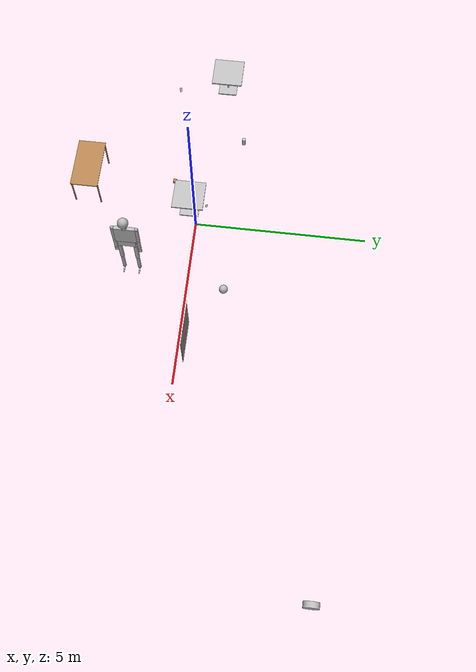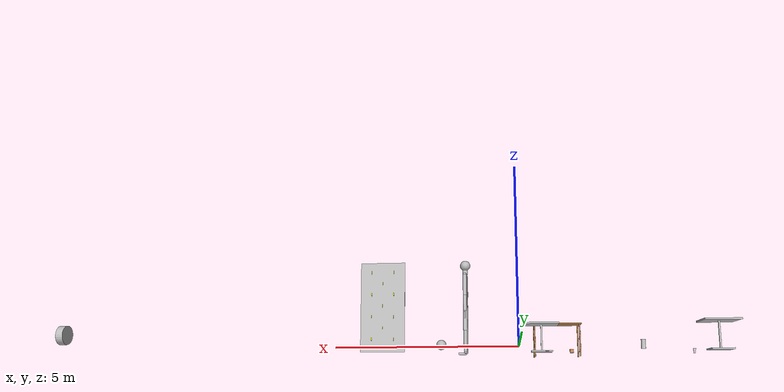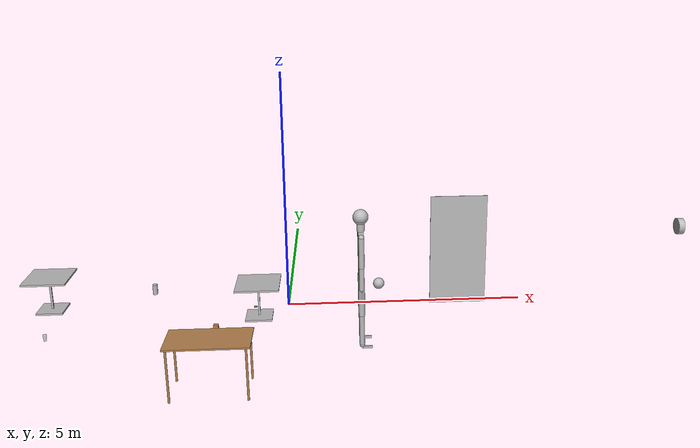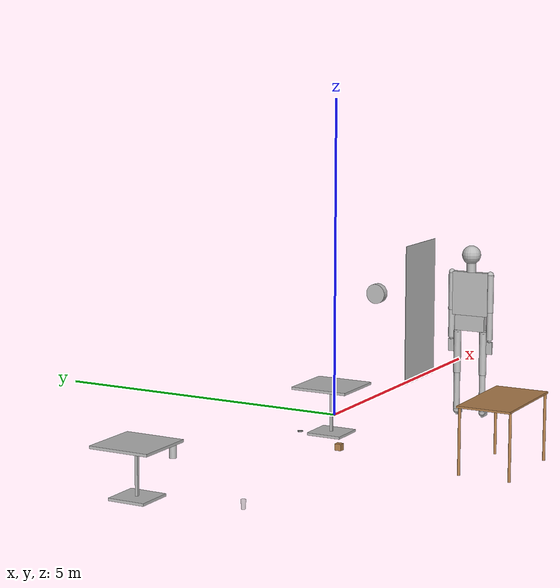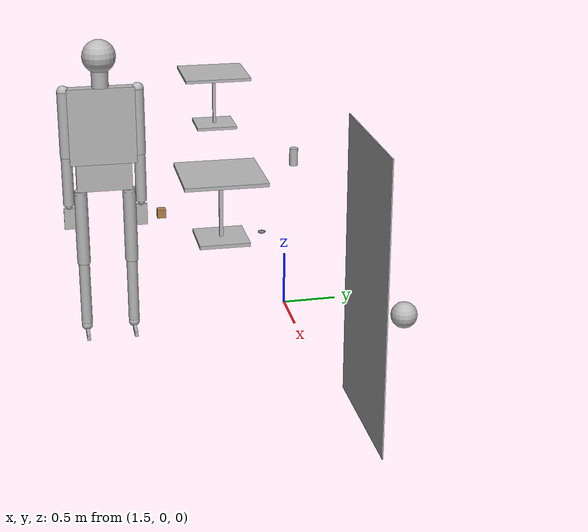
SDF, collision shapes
<?xml version='1.0'?>
<sdf version='1.6'>
  <model name='mynewworld2'>
    <model name='ball_valve_wall'>
      <static>0</static>
      <link name='wall::link'>
        <collision name='collision'>
          <pose frame=''>0.6096 0.00476 1.2192 0 -0 0</pose>
          <geometry>
            <box>
              <size>1.2192 0.00952 2.4384</size>
            </box>
          </geometry>
        </collision>
        <visual name='visual'>
          <pose frame=''>-0.004536 -0.003572 0 0 -0 0</pose>
          <geometry>
            <mesh>
              <uri>model://drc_practice_valve_wall/meshes/five_dice_wall.dae</uri>
            </mesh>
          </geometry>
        </visual>
        <pose frame=''>0 0 0 0 -0 0</pose>
      </link>
      <joint name='wall-joint' type='revolute'>
        <parent>world</parent>
        <child>wall::link</child>
        <axis>
          <xyz>0 0 1</xyz>
          <limit>
            <lower>0</lower>
            <upper>0</upper>
          </limit>
          <use_parent_model_frame>1</use_parent_model_frame>
        </axis>
      </joint>
      <link name='valve_0::handle'>
        <pose frame=''>0.919587 0.0183 0.30722 1.57079 9.3e-05 3.14159</pose>
        <inertial>
          <mass>0.0802</mass>
          <pose frame=''>0 0.0435 0.0055 0 -0 0</pose>
          <inertia>
            <ixx>3.8e-05</ixx>
            <iyy>4e-06</iyy>
            <izz>4e-05</izz>
            <ixy>0</ixy>
            <ixz>0</ixz>
            <iyz>0</iyz>
          </inertia>
        </inertial>
        <collision name='collision'>
          <geometry>
            <mesh>
              <uri>model://drc_practice_ball_valve/meshes/ball_valve.dae</uri>
            </mesh>
          </geometry>
          <surface>
            <bounce>
              <restitution_coefficient>0.01</restitution_coefficient>
              <threshold>5</threshold>
            </bounce>
            <friction>
              <ode>
                <mu>5</mu>
                <mu2>5</mu2>
              </ode>
            </friction>
            <contact>
              <ode>
                <soft_cfm>0.01</soft_cfm>
                <kp>10000</kp>
                <kd>1000</kd>
                <max_vel>0.01</max_vel>
                <min_depth>0.001</min_depth>
              </ode>
            </contact>
          </surface>
        </collision>
        <visual name='visual'>
          <geometry>
            <mesh>
              <uri>model://drc_practice_ball_valve/meshes/ball_valve.dae</uri>
            </mesh>
          </geometry>
        </visual>
      </link>
      <joint name='valve_0::ball' type='revolute'>
        <parent>world</parent>
        <child>valve_0::handle</child>
        <axis>
          <xyz>0 1 0</xyz>
          <limit>
            <lower>0</lower>
            <upper>1.58</upper>
          </limit>
          <dynamics>
            <damping>0.3</damping>
            <friction>10</friction>
            <spring_reference>0</spring_reference>
            <spring_stiffness>0</spring_stiffness>
          </dynamics>
          <use_parent_model_frame>1</use_parent_model_frame>
        </axis>
        <physics>
          <ode>
            <cfm_damping>1</cfm_damping>
          </ode>
        </physics>
      </joint>
      <link name='valve_1::handle'>
        <pose frame=''>0.919587 0.0183 0.91762 1.57079 9.3e-05 3.14159</pose>
        <inertial>
          <mass>0.0802</mass>
          <pose frame=''>0 0.0435 0.0055 0 -0 0</pose>
          <inertia>
            <ixx>3.8e-05</ixx>
            <iyy>4e-06</iyy>
            <izz>4e-05</izz>
            <ixy>0</ixy>
            <ixz>0</ixz>
            <iyz>0</iyz>
          </inertia>
        </inertial>
        <collision name='collision'>
          <geometry>
            <mesh>
              <uri>model://drc_practice_ball_valve/meshes/ball_valve.dae</uri>
            </mesh>
          </geometry>
          <surface>
            <bounce>
              <restitution_coefficient>0.01</restitution_coefficient>
              <threshold>5</threshold>
            </bounce>
            <friction>
              <ode>
                <mu>5</mu>
                <mu2>5</mu2>
              </ode>
            </friction>
            <contact>
              <ode>
                <soft_cfm>0.01</soft_cfm>
                <kp>10000</kp>
                <kd>1000</kd>
                <max_vel>0.01</max_vel>
                <min_depth>0.001</min_depth>
              </ode>
            </contact>
          </surface>
        </collision>
        <visual name='visual'>
          <geometry>
            <mesh>
              <uri>model://drc_practice_ball_valve/meshes/ball_valve.dae</uri>
            </mesh>
          </geometry>
        </visual>
      </link>
      <joint name='valve_1::ball' type='revolute'>
        <parent>world</parent>
        <child>valve_1::handle</child>
        <axis>
          <xyz>0 1 0</xyz>
          <limit>
            <lower>0</lower>
            <upper>1.58</upper>
          </limit>
          <dynamics>
            <damping>0.3</damping>
            <friction>10</friction>
            <spring_reference>0</spring_reference>
            <spring_stiffness>0</spring_stiffness>
          </dynamics>
          <use_parent_model_frame>1</use_parent_model_frame>
        </axis>
        <physics>
          <ode>
            <cfm_damping>1</cfm_damping>
          </ode>
        </physics>
      </joint>
      <link name='valve_2::handle'>
        <pose frame=''>0.919587 0.0183 1.52802 1.57079 9.3e-05 3.14159</pose>
        <inertial>
          <mass>0.0802</mass>
          <pose frame=''>0 0.0435 0.0055 0 -0 0</pose>
          <inertia>
            <ixx>3.8e-05</ixx>
            <iyy>4e-06</iyy>
            <izz>4e-05</izz>
            <ixy>0</ixy>
            <ixz>0</ixz>
            <iyz>0</iyz>
          </inertia>
        </inertial>
        <collision name='collision'>
          <geometry>
            <mesh>
              <uri>model://drc_practice_ball_valve/meshes/ball_valve.dae</uri>
            </mesh>
          </geometry>
          <surface>
            <bounce>
              <restitution_coefficient>0.01</restitution_coefficient>
              <threshold>5</threshold>
            </bounce>
            <friction>
              <ode>
                <mu>5</mu>
                <mu2>5</mu2>
              </ode>
            </friction>
            <contact>
              <ode>
                <soft_cfm>0.01</soft_cfm>
                <kp>10000</kp>
                <kd>1000</kd>
                <max_vel>0.01</max_vel>
                <min_depth>0.001</min_depth>
              </ode>
            </contact>
          </surface>
        </collision>
        <visual name='visual'>
          <geometry>
            <mesh>
              <uri>model://drc_practice_ball_valve/meshes/ball_valve.dae</uri>
            </mesh>
          </geometry>
        </visual>
      </link>
      <joint name='valve_2::ball' type='revolute'>
        <parent>world</parent>
        <child>valve_2::handle</child>
        <axis>
          <xyz>0 1 0</xyz>
          <limit>
            <lower>0</lower>
            <upper>1.58</upper>
          </limit>
          <dynamics>
            <damping>0.3</damping>
            <friction>10</friction>
            <spring_reference>0</spring_reference>
            <spring_stiffness>0</spring_stiffness>
          </dynamics>
          <use_parent_model_frame>1</use_parent_model_frame>
        </axis>
        <physics>
          <ode>
            <cfm_damping>1</cfm_damping>
          </ode>
        </physics>
      </joint>
      <link name='valve_3::handle'>
        <pose frame=''>0.919587 0.0183 2.13842 1.57079 9.3e-05 3.14159</pose>
        <inertial>
          <mass>0.0802</mass>
          <pose frame=''>0 0.0435 0.0055 0 -0 0</pose>
          <inertia>
            <ixx>3.8e-05</ixx>
            <iyy>4e-06</iyy>
            <izz>4e-05</izz>
            <ixy>0</ixy>
            <ixz>0</ixz>
            <iyz>0</iyz>
          </inertia>
        </inertial>
        <collision name='collision'>
          <geometry>
            <mesh>
              <uri>model://drc_practice_ball_valve/meshes/ball_valve.dae</uri>
            </mesh>
          </geometry>
          <surface>
            <bounce>
              <restitution_coefficient>0.01</restitution_coefficient>
              <threshold>5</threshold>
            </bounce>
            <friction>
              <ode>
                <mu>5</mu>
                <mu2>5</mu2>
              </ode>
            </friction>
            <contact>
              <ode>
                <soft_cfm>0.01</soft_cfm>
                <kp>10000</kp>
                <kd>1000</kd>
                <max_vel>0.01</max_vel>
                <min_depth>0.001</min_depth>
              </ode>
            </contact>
          </surface>
        </collision>
        <visual name='visual'>
          <geometry>
            <mesh>
              <uri>model://drc_practice_ball_valve/meshes/ball_valve.dae</uri>
            </mesh>
          </geometry>
        </visual>
      </link>
      <joint name='valve_3::ball' type='revolute'>
        <parent>world</parent>
        <child>valve_3::handle</child>
        <axis>
          <xyz>0 1 0</xyz>
          <limit>
            <lower>0</lower>
            <upper>1.58</upper>
          </limit>
          <dynamics>
            <damping>0.3</damping>
            <friction>10</friction>
            <spring_reference>0</spring_reference>
            <spring_stiffness>0</spring_stiffness>
          </dynamics>
          <use_parent_model_frame>1</use_parent_model_frame>
        </axis>
        <physics>
          <ode>
            <cfm_damping>1</cfm_damping>
          </ode>
        </physics>
      </joint>
      <link name='valve_4::handle'>
        <pose frame=''>0.614335 0.0183 0.61182 1.57079 9.3e-05 3.14159</pose>
        <inertial>
          <mass>0.0802</mass>
          <pose frame=''>0 0.0435 0.0055 0 -0 0</pose>
          <inertia>
            <ixx>3.8e-05</ixx>
            <iyy>4e-06</iyy>
            <izz>4e-05</izz>
            <ixy>0</ixy>
            <ixz>0</ixz>
            <iyz>0</iyz>
          </inertia>
        </inertial>
        <collision name='collision'>
          <geometry>
            <mesh>
              <uri>model://drc_practice_ball_valve/meshes/ball_valve.dae</uri>
            </mesh>
          </geometry>
          <surface>
            <bounce>
              <restitution_coefficient>0.01</restitution_coefficient>
              <threshold>5</threshold>
            </bounce>
            <friction>
              <ode>
                <mu>5</mu>
                <mu2>5</mu2>
              </ode>
            </friction>
            <contact>
              <ode>
                <soft_cfm>0.01</soft_cfm>
                <kp>10000</kp>
                <kd>1000</kd>
                <max_vel>0.01</max_vel>
                <min_depth>0.001</min_depth>
              </ode>
            </contact>
          </surface>
        </collision>
        <visual name='visual'>
          <geometry>
            <mesh>
              <uri>model://drc_practice_ball_valve/meshes/ball_valve.dae</uri>
            </mesh>
          </geometry>
        </visual>
      </link>
      <joint name='valve_4::ball' type='revolute'>
        <parent>world</parent>
        <child>valve_4::handle</child>
        <axis>
          <xyz>0 1 0</xyz>
          <limit>
            <lower>0</lower>
            <upper>1.58</upper>
          </limit>
          <dynamics>
            <damping>0.3</damping>
            <friction>10</friction>
            <spring_reference>0</spring_reference>
            <spring_stiffness>0</spring_stiffness>
          </dynamics>
          <use_parent_model_frame>1</use_parent_model_frame>
        </axis>
        <physics>
          <ode>
            <cfm_damping>1</cfm_damping>
          </ode>
        </physics>
      </joint>
      <link name='valve_5::handle'>
        <pose frame=''>0.614335 0.0183 1.22222 1.57079 9.3e-05 3.14159</pose>
        <inertial>
          <mass>0.0802</mass>
          <pose frame=''>0 0.0435 0.0055 0 -0 0</pose>
          <inertia>
            <ixx>3.8e-05</ixx>
            <iyy>4e-06</iyy>
            <izz>4e-05</izz>
            <ixy>0</ixy>
            <ixz>0</ixz>
            <iyz>0</iyz>
          </inertia>
        </inertial>
        <collision name='collision'>
          <geometry>
            <mesh>
              <uri>model://drc_practice_ball_valve/meshes/ball_valve.dae</uri>
            </mesh>
          </geometry>
          <surface>
            <bounce>
              <restitution_coefficient>0.01</restitution_coefficient>
              <threshold>5</threshold>
            </bounce>
            <friction>
              <ode>
                <mu>5</mu>
                <mu2>5</mu2>
              </ode>
            </friction>
            <contact>
              <ode>
                <soft_cfm>0.01</soft_cfm>
                <kp>10000</kp>
                <kd>1000</kd>
                <max_vel>0.01</max_vel>
                <min_depth>0.001</min_depth>
              </ode>
            </contact>
          </surface>
        </collision>
        <visual name='visual'>
          <geometry>
            <mesh>
              <uri>model://drc_practice_ball_valve/meshes/ball_valve.dae</uri>
            </mesh>
          </geometry>
        </visual>
      </link>
      <joint name='valve_5::ball' type='revolute'>
        <parent>world</parent>
        <child>valve_5::handle</child>
        <axis>
          <xyz>0 1 0</xyz>
          <limit>
            <lower>0</lower>
            <upper>1.58</upper>
          </limit>
          <dynamics>
            <damping>0.3</damping>
            <friction>10</friction>
            <spring_reference>0</spring_reference>
            <spring_stiffness>0</spring_stiffness>
          </dynamics>
          <use_parent_model_frame>1</use_parent_model_frame>
        </axis>
        <physics>
          <ode>
            <cfm_damping>1</cfm_damping>
          </ode>
        </physics>
      </joint>
      <link name='valve_6::handle'>
        <pose frame=''>0.614335 0.0183 1.83262 1.57079 9.3e-05 3.14159</pose>
        <inertial>
          <mass>0.0802</mass>
          <pose frame=''>0 0.0435 0.0055 0 -0 0</pose>
          <inertia>
            <ixx>3.8e-05</ixx>
            <iyy>4e-06</iyy>
            <izz>4e-05</izz>
            <ixy>0</ixy>
            <ixz>0</ixz>
            <iyz>0</iyz>
          </inertia>
        </inertial>
        <collision name='collision'>
          <geometry>
            <mesh>
              <uri>model://drc_practice_ball_valve/meshes/ball_valve.dae</uri>
            </mesh>
          </geometry>
          <surface>
            <bounce>
              <restitution_coefficient>0.01</restitution_coefficient>
              <threshold>5</threshold>
            </bounce>
            <friction>
              <ode>
                <mu>5</mu>
                <mu2>5</mu2>
              </ode>
            </friction>
            <contact>
              <ode>
                <soft_cfm>0.01</soft_cfm>
                <kp>10000</kp>
                <kd>1000</kd>
                <max_vel>0.01</max_vel>
                <min_depth>0.001</min_depth>
              </ode>
            </contact>
          </surface>
        </collision>
        <visual name='visual'>
          <geometry>
            <mesh>
              <uri>model://drc_practice_ball_valve/meshes/ball_valve.dae</uri>
            </mesh>
          </geometry>
        </visual>
      </link>
      <joint name='valve_6::ball' type='revolute'>
        <parent>world</parent>
        <child>valve_6::handle</child>
        <axis>
          <xyz>0 1 0</xyz>
          <limit>
            <lower>0</lower>
            <upper>1.58</upper>
          </limit>
          <dynamics>
            <damping>0.3</damping>
            <friction>10</friction>
            <spring_reference>0</spring_reference>
            <spring_stiffness>0</spring_stiffness>
          </dynamics>
          <use_parent_model_frame>1</use_parent_model_frame>
        </axis>
        <physics>
          <ode>
            <cfm_damping>1</cfm_damping>
          </ode>
        </physics>
      </joint>
      <link name='valve_7::handle'>
        <pose frame=''>0.309083 0.0183 0.30722 1.57079 9.3e-05 3.14159</pose>
        <inertial>
          <mass>0.0802</mass>
          <pose frame=''>0 0.0435 0.0055 0 -0 0</pose>
          <inertia>
            <ixx>3.8e-05</ixx>
            <iyy>4e-06</iyy>
            <izz>4e-05</izz>
            <ixy>0</ixy>
            <ixz>0</ixz>
            <iyz>0</iyz>
          </inertia>
        </inertial>
        <collision name='collision'>
          <geometry>
            <mesh>
              <uri>model://drc_practice_ball_valve/meshes/ball_valve.dae</uri>
            </mesh>
          </geometry>
          <surface>
            <bounce>
              <restitution_coefficient>0.01</restitution_coefficient>
              <threshold>5</threshold>
            </bounce>
            <friction>
              <ode>
                <mu>5</mu>
                <mu2>5</mu2>
              </ode>
            </friction>
            <contact>
              <ode>
                <soft_cfm>0.01</soft_cfm>
                <kp>10000</kp>
                <kd>1000</kd>
                <max_vel>0.01</max_vel>
                <min_depth>0.001</min_depth>
              </ode>
            </contact>
          </surface>
        </collision>
        <visual name='visual'>
          <geometry>
            <mesh>
              <uri>model://drc_practice_ball_valve/meshes/ball_valve.dae</uri>
            </mesh>
          </geometry>
        </visual>
      </link>
      <joint name='valve_7::ball' type='revolute'>
        <parent>world</parent>
        <child>valve_7::handle</child>
        <axis>
          <xyz>0 1 0</xyz>
          <limit>
            <lower>0</lower>
            <upper>1.58</upper>
          </limit>
          <dynamics>
            <damping>0.3</damping>
            <friction>10</friction>
            <spring_reference>0</spring_reference>
            <spring_stiffness>0</spring_stiffness>
          </dynamics>
          <use_parent_model_frame>1</use_parent_model_frame>
        </axis>
        <physics>
          <ode>
            <cfm_damping>1</cfm_damping>
          </ode>
        </physics>
      </joint>
      <link name='valve_8::handle'>
        <pose frame=''>0.309083 0.0183 0.91762 1.57079 9.3e-05 3.14159</pose>
        <inertial>
          <mass>0.0802</mass>
          <pose frame=''>0 0.0435 0.0055 0 -0 0</pose>
          <inertia>
            <ixx>3.8e-05</ixx>
            <iyy>4e-06</iyy>
            <izz>4e-05</izz>
            <ixy>0</ixy>
            <ixz>0</ixz>
            <iyz>0</iyz>
          </inertia>
        </inertial>
        <collision name='collision'>
          <geometry>
            <mesh>
              <uri>model://drc_practice_ball_valve/meshes/ball_valve.dae</uri>
            </mesh>
          </geometry>
          <surface>
            <bounce>
              <restitution_coefficient>0.01</restitution_coefficient>
              <threshold>5</threshold>
            </bounce>
            <friction>
              <ode>
                <mu>5</mu>
                <mu2>5</mu2>
              </ode>
            </friction>
            <contact>
              <ode>
                <soft_cfm>0.01</soft_cfm>
                <kp>10000</kp>
                <kd>1000</kd>
                <max_vel>0.01</max_vel>
                <min_depth>0.001</min_depth>
              </ode>
            </contact>
          </surface>
        </collision>
        <visual name='visual'>
          <geometry>
            <mesh>
              <uri>model://drc_practice_ball_valve/meshes/ball_valve.dae</uri>
            </mesh>
          </geometry>
        </visual>
      </link>
      <joint name='valve_8::ball' type='revolute'>
        <parent>world</parent>
        <child>valve_8::handle</child>
        <axis>
          <xyz>0 1 0</xyz>
          <limit>
            <lower>0</lower>
            <upper>1.58</upper>
          </limit>
          <dynamics>
            <damping>0.3</damping>
            <friction>10</friction>
            <spring_reference>0</spring_reference>
            <spring_stiffness>0</spring_stiffness>
          </dynamics>
          <use_parent_model_frame>1</use_parent_model_frame>
        </axis>
        <physics>
          <ode>
            <cfm_damping>1</cfm_damping>
          </ode>
        </physics>
      </joint>
      <link name='valve_9::handle'>
        <pose frame=''>0.309083 0.0183 1.52802 1.57079 9.3e-05 3.14159</pose>
        <inertial>
          <mass>0.0802</mass>
          <pose frame=''>0 0.0435 0.0055 0 -0 0</pose>
          <inertia>
            <ixx>3.8e-05</ixx>
            <iyy>4e-06</iyy>
            <izz>4e-05</izz>
            <ixy>0</ixy>
            <ixz>0</ixz>
            <iyz>0</iyz>
          </inertia>
        </inertial>
        <collision name='collision'>
          <geometry>
            <mesh>
              <uri>model://drc_practice_ball_valve/meshes/ball_valve.dae</uri>
            </mesh>
          </geometry>
          <surface>
            <bounce>
              <restitution_coefficient>0.01</restitution_coefficient>
              <threshold>5</threshold>
            </bounce>
            <friction>
              <ode>
                <mu>5</mu>
                <mu2>5</mu2>
              </ode>
            </friction>
            <contact>
              <ode>
                <soft_cfm>0.01</soft_cfm>
                <kp>10000</kp>
                <kd>1000</kd>
                <max_vel>0.01</max_vel>
                <min_depth>0.001</min_depth>
              </ode>
            </contact>
          </surface>
        </collision>
        <visual name='visual'>
          <geometry>
            <mesh>
              <uri>model://drc_practice_ball_valve/meshes/ball_valve.dae</uri>
            </mesh>
          </geometry>
        </visual>
      </link>
      <joint name='valve_9::ball' type='revolute'>
        <parent>world</parent>
        <child>valve_9::handle</child>
        <axis>
          <xyz>0 1 0</xyz>
          <limit>
            <lower>0</lower>
            <upper>1.58</upper>
          </limit>
          <dynamics>
            <damping>0.3</damping>
            <friction>10</friction>
            <spring_reference>0</spring_reference>
            <spring_stiffness>0</spring_stiffness>
          </dynamics>
          <use_parent_model_frame>1</use_parent_model_frame>
        </axis>
        <physics>
          <ode>
            <cfm_damping>1</cfm_damping>
          </ode>
        </physics>
      </joint>
      <link name='valve_10::handle'>
        <pose frame=''>0.309083 0.0183 2.13842 1.57079 9.3e-05 3.14159</pose>
        <inertial>
          <mass>0.0802</mass>
          <pose frame=''>0 0.0435 0.0055 0 -0 0</pose>
          <inertia>
            <ixx>3.8e-05</ixx>
            <iyy>4e-06</iyy>
            <izz>4e-05</izz>
            <ixy>0</ixy>
            <ixz>0</ixz>
            <iyz>0</iyz>
          </inertia>
        </inertial>
        <collision name='collision'>
          <geometry>
            <mesh>
              <uri>model://drc_practice_ball_valve/meshes/ball_valve.dae</uri>
            </mesh>
          </geometry>
          <surface>
            <bounce>
              <restitution_coefficient>0.01</restitution_coefficient>
              <threshold>5</threshold>
            </bounce>
            <friction>
              <ode>
                <mu>5</mu>
                <mu2>5</mu2>
              </ode>
            </friction>
            <contact>
              <ode>
                <soft_cfm>0.01</soft_cfm>
                <kp>10000</kp>
                <kd>1000</kd>
                <max_vel>0.01</max_vel>
                <min_depth>0.001</min_depth>
              </ode>
            </contact>
          </surface>
        </collision>
        <visual name='visual'>
          <geometry>
            <mesh>
              <uri>model://drc_practice_ball_valve/meshes/ball_valve.dae</uri>
            </mesh>
          </geometry>
        </visual>
      </link>
      <joint name='valve_10::ball' type='revolute'>
        <parent>world</parent>
        <child>valve_10::handle</child>
        <axis>
          <xyz>0 1 0</xyz>
          <limit>
            <lower>0</lower>
            <upper>1.58</upper>
          </limit>
          <dynamics>
            <damping>0.3</damping>
            <friction>10</friction>
            <spring_reference>0</spring_reference>
            <spring_stiffness>0</spring_stiffness>
          </dynamics>
          <use_parent_model_frame>1</use_parent_model_frame>
        </axis>
        <physics>
          <ode>
            <cfm_damping>1</cfm_damping>
          </ode>
        </physics>
      </joint>
      <pose frame=''>3.06184 0.187688 -0.138818 0 -0 0</pose>
    </model>
    <model name='beer'>
      <link name='link'>
        <pose frame=''>0 0 0.115 0 -0 0</pose>
        <inertial>
          <mass>0.39</mass>
          <inertia>
            <ixx>0.00058</ixx>
            <ixy>0</ixy>
            <ixz>0</ixz>
            <iyy>0.00058</iyy>
            <iyz>0</iyz>
            <izz>0.00019</izz>
          </inertia>
        </inertial>
        <collision name='collision'>
          <geometry>
            <cylinder>
              <radius>0.055</radius>
              <length>0.23</length>
            </cylinder>
          </geometry>
        </collision>
        <visual name='visual'>
          <geometry>
            <cylinder>
              <radius>0.055</radius>
              <length>0.23</length>
            </cylinder>
          </geometry>
          <material>
            <script>
              <uri>model://beer/materials/scripts</uri>
              <uri>model://beer/materials/textures</uri>
              <name>Beer/Diffuse</name>
            </script>
          </material>
        </visual>
      </link>
      <pose frame=''>-3.05054 1.09308 -0.138818 0 -0 0</pose>
    </model>
    <model name='cafe_table'>
      <static>1</static>
      <link name='link'>
        <collision name='surface'>
          <pose frame=''>0 0 0.755 0 -0 0</pose>
          <geometry>
            <box>
              <size>0.913 0.913 0.04</size>
            </box>
          </geometry>
        </collision>
        <collision name='column'>
          <pose frame=''>0 0 0.37 0 -0 0</pose>
          <geometry>
            <box>
              <size>0.042 0.042 0.74</size>
            </box>
          </geometry>
        </collision>
        <collision name='base'>
          <pose frame=''>0 0 0.02 0 -0 0</pose>
          <geometry>
            <box>
              <size>0.56 0.56 0.04</size>
            </box>
          </geometry>
        </collision>
        <visual name='visual'>
          <geometry>
            <mesh>
              <uri>model://cafe_table/meshes/cafe_table.dae</uri>
            </mesh>
          </geometry>
        </visual>
      </link>
      <pose frame=''>-5.08616 0.377168 -0.138818 0 -0 0</pose>
    </model>
    <model name='cafe_table_0'>
      <static>1</static>
      <link name='link'>
        <collision name='surface'>
          <pose frame=''>0 0 0.755 0 -0 0</pose>
          <geometry>
            <box>
              <size>0.913 0.913 0.04</size>
            </box>
          </geometry>
        </collision>
        <collision name='column'>
          <pose frame=''>0 0 0.37 0 -0 0</pose>
          <geometry>
            <box>
              <size>0.042 0.042 0.74</size>
            </box>
          </geometry>
        </collision>
        <collision name='base'>
          <pose frame=''>0 0 0.02 0 -0 0</pose>
          <geometry>
            <box>
              <size>0.56 0.56 0.04</size>
            </box>
          </geometry>
        </collision>
        <visual name='visual'>
          <geometry>
            <mesh>
              <uri>model://cafe_table/meshes/cafe_table.dae</uri>
            </mesh>
          </geometry>
        </visual>
      </link>
      <pose frame=''>-0.61129 -0.2621 -0.138818 0 -0 0</pose>
    </model>
    <model name='car_wheel'>
      <link name='link'>
        <pose frame=''>0 0 0.21682 0 1.5707 0</pose>
        <inertial>
          <mass>12</mass>
          <inertia>
            <ixx>0.167005</ixx>
            <ixy>0</ixy>
            <ixz>0</ixz>
            <iyy>0.167005</iyy>
            <iyz>0</iyz>
            <izz>0.282065</izz>
          </inertia>
        </inertial>
        <collision name='collision'>
          <geometry>
            <cylinder>
              <radius>0.21682</radius>
              <length>0.16116</length>
            </cylinder>
          </geometry>
          <surface>
            <friction>
              <ode>
                <mu>1</mu>
                <mu2>1</mu2>
                <fdir1>0 0 1</fdir1>
                <slip1>0</slip1>
                <slip2>0</slip2>
              </ode>
            </friction>
            <contact>
              <ode>
                <min_depth>0.005</min_depth>
                <kp>1e+08</kp>
              </ode>
            </contact>
          </surface>
        </collision>
        <visual name='visual'>
          <pose frame=''>0 0 -0.08058 0 -0 0</pose>
          <geometry>
            <mesh>
              <uri>model://car_wheel/meshes/car_wheel.dae</uri>
            </mesh>
          </geometry>
        </visual>
      </link>
      <pose frame=''>10.3569 4.2479 -0.138818 0 -0 0</pose>
    </model>
    <model name='frc2016_ball'>
      <pose frame=''>1.99171 1.05475 -0.011818 0 -0 0</pose>
      <link name='link'>
        <inertial>
          <mass>0.213</mass>
          <inertia>
            <ixx>0.00322667</ixx>
            <ixy>0</ixy>
            <ixz>0</ixz>
            <iyy>0.00322667</iyy>
            <iyz>0</iyz>
            <izz>0.00322667</izz>
          </inertia>
        </inertial>
        <visual name='visual'>
          <geometry>
            <sphere>
              <radius>0.127</radius>
            </sphere>
          </geometry>
        </visual>
        <collision name='collision'>
          <geometry>
            <sphere>
              <radius>0.127</radius>
            </sphere>
          </geometry>
          <surface>
            <bounce>
              <restitution_coefficient>0.15937</restitution_coefficient>
              <threshold>0</threshold>
            </bounce>
            <contact>
              <ode>
                <max_vel>100</max_vel>
                <min_depth>0.001</min_depth>
              </ode>
            </contact>
          </surface>
        </collision>
      </link>
    </model>
    <model name='plastic_cup'>
      <link name='link'>
        <pose frame=''>0 0 0.065 0 -0 0</pose>
        <inertial>
          <mass>0.0599</mass>
          <inertia>
            <ixx>0.000302896</ixx>
            <ixy>0</ixy>
            <ixz>0</ixz>
            <iyy>0.000302896</iyy>
            <iyz>0</iyz>
            <izz>3.28764e-05</izz>
          </inertia>
        </inertial>
        <collision name='collision'>
          <geometry>
            <mesh>
              <uri>model://plastic_cup/meshes/plastic_cup.dae</uri>
            </mesh>
          </geometry>
          <surface>
            <contact>
              <poissons_ratio>0.35</poissons_ratio>
              <elastic_modulus>3.10264e+09</elastic_modulus>
              <ode>
                <kp>100000</kp>
                <kd>100</kd>
                <max_vel>100</max_vel>
                <min_depth>0.001</min_depth>
              </ode>
            </contact>
            <friction>
              <torsional>
                <coefficient>1</coefficient>
                <use_patch_radius>0</use_patch_radius>
                <surface_radius>0.01</surface_radius>
              </torsional>
            </friction>
          </surface>
        </collision>
        <visual name='visual'>
          <geometry>
            <mesh>
              <uri>model://plastic_cup/meshes/plastic_cup.dae</uri>
            </mesh>
          </geometry>
          <material>
            <script>
              <uri>file://media/materials/scripts/gazebo.material</uri>
              <name>Gazebo/GreyTransparent</name>
            </script>
          </material>
        </visual>
      </link>
      <pose frame=''>-4.78589 -1.1093 -0.138818 0 -0 0</pose>
    </model>
    <model name='ragdoll'>
      <pose frame=''>1.51221 -1.66515 1.26118 0 -0 0</pose>
      <link name='hip'>
        <inertial>
          <inertia>
            <ixx>0.1</ixx>
            <ixy>0</ixy>
            <ixz>0</ixz>
            <iyy>0.1</iyy>
            <iyz>0</iyz>
            <izz>0.1</izz>
          </inertia>
          <mass>10</mass>
        </inertial>
        <collision name='hip_geom'>
          <pose frame=''>0 0 0.125 0 -0 0</pose>
          <geometry>
            <box>
              <size>0.1 0.5 0.25</size>
            </box>
          </geometry>
          <surface>
            <friction>
              <ode>
                <mu>-1</mu>
                <mu2>-1</mu2>
                <fdir1>0 0 0</fdir1>
                <slip1>0</slip1>
                <slip2>0</slip2>
              </ode>
            </friction>
            <bounce>
              <restitution_coefficient>0</restitution_coefficient>
              <threshold>100000</threshold>
            </bounce>
            <contact>
              <ode>
                <soft_cfm>0</soft_cfm>
                <soft_erp>0.2</soft_erp>
                <kp>1e+12</kp>
                <kd>1</kd>
                <max_vel>0</max_vel>
                <min_depth>0.001</min_depth>
              </ode>
            </contact>
          </surface>
          <laser_retro>0</laser_retro>
        </collision>
        <visual name='hip_geom_visual'>
          <pose frame=''>0 0 0.125 0 -0 0</pose>
          <geometry>
            <box>
              <size>0.1 0.5 0.25</size>
            </box>
          </geometry>
          <cast_shadows>1</cast_shadows>
          <laser_retro>0</laser_retro>
          <transparency>0</transparency>
        </visual>
        <gravity>0</gravity>
        <self_collide>0</self_collide>
        <kinematic>0</kinematic>
      </link>
      <link name='l_thigh_pan'>
        <pose frame=''>0 0.22 0 0 -0 0</pose>
        <inertial>
          <inertia>
            <ixx>0.01</ixx>
            <ixy>0</ixy>
            <ixz>0</ixz>
            <iyy>0.01</iyy>
            <iyz>0</iyz>
            <izz>0.01</izz>
          </inertia>
          <mass>1</mass>
        </inertial>
        <collision name='l_thigh_pan_geom'>
          <pose frame=''>0 0 -0.03 0 -0 0</pose>
          <geometry>
            <sphere>
              <radius>0.06</radius>
            </sphere>
          </geometry>
          <surface>
            <friction>
              <ode>
                <mu>-1</mu>
                <mu2>-1</mu2>
                <fdir1>0 0 0</fdir1>
                <slip1>0</slip1>
                <slip2>0</slip2>
              </ode>
            </friction>
            <bounce>
              <restitution_coefficient>0</restitution_coefficient>
              <threshold>100000</threshold>
            </bounce>
            <contact>
              <ode>
                <soft_cfm>0</soft_cfm>
                <soft_erp>0.2</soft_erp>
                <kp>1e+12</kp>
                <kd>1</kd>
                <max_vel>0</max_vel>
                <min_depth>0.001</min_depth>
              </ode>
            </contact>
          </surface>
          <laser_retro>0</laser_retro>
        </collision>
        <visual name='l_thigh_pan_geom_visual'>
          <pose frame=''>0 0 -0.03 0 -0 0</pose>
          <geometry>
            <sphere>
              <radius>0.06</radius>
            </sphere>
          </geometry>
          <cast_shadows>1</cast_shadows>
          <laser_retro>0</laser_retro>
          <transparency>0</transparency>
        </visual>
        <gravity>0</gravity>
        <self_collide>0</self_collide>
        <kinematic>0</kinematic>
      </link>
      <link name='l_thigh_lift'>
        <pose frame=''>0 0.22 0 0 -0 0</pose>
        <inertial>
          <inertia>
            <ixx>0.05</ixx>
            <ixy>0</ixy>
            <ixz>0</ixz>
            <iyy>0.05</iyy>
            <iyz>0</iyz>
            <izz>0.05</izz>
          </inertia>
          <mass>5</mass>
        </inertial>
        <collision name='l_thigh_lift_geom'>
          <pose frame=''>0 0 -0.35 0 -0 0</pose>
          <geometry>
            <cylinder>
              <radius>0.06</radius>
              <length>0.7</length>
            </cylinder>
          </geometry>
          <surface>
            <friction>
              <ode>
                <mu>-1</mu>
                <mu2>-1</mu2>
                <fdir1>0 0 0</fdir1>
                <slip1>0</slip1>
                <slip2>0</slip2>
              </ode>
            </friction>
            <bounce>
              <restitution_coefficient>0</restitution_coefficient>
              <threshold>100000</threshold>
            </bounce>
            <contact>
              <ode>
                <soft_cfm>0</soft_cfm>
                <soft_erp>0.2</soft_erp>
                <kp>1e+12</kp>
                <kd>1</kd>
                <max_vel>0</max_vel>
                <min_depth>0.001</min_depth>
              </ode>
            </contact>
          </surface>
          <laser_retro>0</laser_retro>
        </collision>
        <visual name='l_thigh_lift_geom_visual'>
          <pose frame=''>0 0 -0.35 0 -0 0</pose>
          <geometry>
            <cylinder>
              <radius>0.06</radius>
              <length>0.7</length>
            </cylinder>
          </geometry>
          <cast_shadows>1</cast_shadows>
          <laser_retro>0</laser_retro>
          <transparency>0</transparency>
        </visual>
        <gravity>0</gravity>
        <self_collide>0</self_collide>
        <kinematic>0</kinematic>
      </link>
      <link name='l_calf'>
        <pose frame=''>0 0.22 -0.7 0 -0 0</pose>
        <inertial>
          <inertia>
            <ixx>0.02</ixx>
            <ixy>0</ixy>
            <ixz>0</ixz>
            <iyy>0.02</iyy>
            <iyz>0</iyz>
            <izz>0.02</izz>
          </inertia>
          <mass>2</mass>
        </inertial>
        <collision name='l_calf_geom'>
          <pose frame=''>0 0 -0.3 0 -0 0</pose>
          <geometry>
            <cylinder>
              <radius>0.05</radius>
              <length>0.6</length>
            </cylinder>
          </geometry>
          <surface>
            <friction>
              <ode>
                <mu>-1</mu>
                <mu2>-1</mu2>
                <fdir1>0 0 0</fdir1>
                <slip1>0</slip1>
                <slip2>0</slip2>
              </ode>
            </friction>
            <bounce>
              <restitution_coefficient>0</restitution_coefficient>
              <threshold>100000</threshold>
            </bounce>
            <contact>
              <ode>
                <soft_cfm>0</soft_cfm>
                <soft_erp>0.2</soft_erp>
                <kp>1e+12</kp>
                <kd>1</kd>
                <max_vel>0</max_vel>
                <min_depth>0.001</min_depth>
              </ode>
            </contact>
          </surface>
          <laser_retro>0</laser_retro>
        </collision>
        <visual name='l_calf_geom_visual'>
          <pose frame=''>0 0 -0.3 0 -0 0</pose>
          <geometry>
            <cylinder>
              <radius>0.05</radius>
              <length>0.6</length>
            </cylinder>
          </geometry>
          <cast_shadows>1</cast_shadows>
          <laser_retro>0</laser_retro>
          <transparency>0</transparency>
        </visual>
        <gravity>0</gravity>
        <self_collide>0</self_collide>
        <kinematic>0</kinematic>
      </link>
      <link name='l_ankle'>
        <pose frame=''>0 0.22 -1.325 0 -0 0</pose>
        <inertial>
          <inertia>
            <ixx>0.01</ixx>
            <ixy>0</ixy>
            <ixz>0</ixz>
            <iyy>0.01</iyy>
            <iyz>0</iyz>
            <izz>0.01</izz>
          </inertia>
          <mass>1</mass>
        </inertial>
        <collision name='l_ankle_geom'>
          <geometry>
            <sphere>
              <radius>0.05</radius>
            </sphere>
          </geometry>
          <surface>
            <friction>
              <ode>
                <mu>-1</mu>
                <mu2>-1</mu2>
                <fdir1>0 0 0</fdir1>
                <slip1>0</slip1>
                <slip2>0</slip2>
              </ode>
            </friction>
            <bounce>
              <restitution_coefficient>0</restitution_coefficient>
              <threshold>100000</threshold>
            </bounce>
            <contact>
              <ode>
                <soft_cfm>0</soft_cfm>
                <soft_erp>0.2</soft_erp>
                <kp>1e+12</kp>
                <kd>1</kd>
                <max_vel>0</max_vel>
                <min_depth>0.001</min_depth>
              </ode>
            </contact>
          </surface>
          <laser_retro>0</laser_retro>
        </collision>
        <visual name='l_ankle_geom_visual'>
          <geometry>
            <sphere>
              <radius>0.05</radius>
            </sphere>
          </geometry>
          <cast_shadows>1</cast_shadows>
          <laser_retro>0</laser_retro>
          <transparency>0</transparency>
        </visual>
        <gravity>0</gravity>
        <self_collide>0</self_collide>
        <kinematic>0</kinematic>
      </link>
      <link name='l_foot'>
        <pose frame=''>0 0.22 -1.35 0 -0 0</pose>
        <inertial>
          <pose frame=''>0.1 0 0 0 -0 0</pose>
          <inertia>
            <ixx>0.01</ixx>
            <ixy>0</ixy>
            <ixz>0</ixz>
            <iyy>0.01</iyy>
            <iyz>0</iyz>
            <izz>0.01</izz>
          </inertia>
          <mass>1</mass>
        </inertial>
        <collision name='l_foot_geom'>
          <pose frame=''>0.1 0 -0.025 0 -0 0</pose>
          <geometry>
            <box>
              <size>0.2 0.03 0.05</size>
            </box>
          </geometry>
          <surface>
            <friction>
              <ode>
                <mu>-1</mu>
                <mu2>-1</mu2>
                <fdir1>0 0 0</fdir1>
                <slip1>0</slip1>
                <slip2>0</slip2>
              </ode>
            </friction>
            <bounce>
              <restitution_coefficient>0</restitution_coefficient>
              <threshold>100000</threshold>
            </bounce>
            <contact>
              <ode>
                <soft_cfm>0</soft_cfm>
                <soft_erp>0.2</soft_erp>
                <kp>1e+12</kp>
                <kd>1</kd>
                <max_vel>0</max_vel>
                <min_depth>0.001</min_depth>
              </ode>
            </contact>
          </surface>
          <laser_retro>0</laser_retro>
        </collision>
        <visual name='l_foot_geom_visual'>
          <pose frame=''>0.1 0 -0.025 0 -0 0</pose>
          <geometry>
            <box>
              <size>0.2 0.03 0.05</size>
            </box>
          </geometry>
          <cast_shadows>1</cast_shadows>
          <laser_retro>0</laser_retro>
          <transparency>0</transparency>
        </visual>
        <gravity>1</gravity>
        <self_collide>0</self_collide>
        <kinematic>0</kinematic>
      </link>
      <link name='r_thigh_pan'>
        <pose frame=''>0 -0.22 0 0 -0 0</pose>
        <inertial>
          <inertia>
            <ixx>0.01</ixx>
            <ixy>0</ixy>
            <ixz>0</ixz>
            <iyy>0.01</iyy>
            <iyz>0</iyz>
            <izz>0.01</izz>
          </inertia>
          <mass>1</mass>
        </inertial>
        <collision name='r_thigh_pan_geom'>
          <pose frame=''>0 0 -0.03 0 -0 0</pose>
          <geometry>
            <sphere>
              <radius>0.06</radius>
            </sphere>
          </geometry>
          <surface>
            <friction>
              <ode>
                <mu>-1</mu>
                <mu2>-1</mu2>
                <fdir1>0 0 0</fdir1>
                <slip1>0</slip1>
                <slip2>0</slip2>
              </ode>
            </friction>
            <bounce>
              <restitution_coefficient>0</restitution_coefficient>
              <threshold>100000</threshold>
            </bounce>
            <contact>
              <ode>
                <soft_cfm>0</soft_cfm>
                <soft_erp>0.2</soft_erp>
                <kp>1e+12</kp>
                <kd>1</kd>
                <max_vel>0</max_vel>
                <min_depth>0.001</min_depth>
              </ode>
            </contact>
          </surface>
          <laser_retro>0</laser_retro>
        </collision>
        <visual name='r_thigh_pan_geom_visual'>
          <pose frame=''>0 0 -0.03 0 -0 0</pose>
          <geometry>
            <sphere>
              <radius>0.06</radius>
            </sphere>
          </geometry>
          <cast_shadows>1</cast_shadows>
          <laser_retro>0</laser_retro>
          <transparency>0</transparency>
        </visual>
        <gravity>0</gravity>
        <self_collide>0</self_collide>
        <kinematic>0</kinematic>
      </link>
      <link name='r_thigh_lift'>
        <pose frame=''>0 -0.22 0 0 -0 0</pose>
        <inertial>
          <inertia>
            <ixx>0.05</ixx>
            <ixy>0</ixy>
            <ixz>0</ixz>
            <iyy>0.05</iyy>
            <iyz>0</iyz>
            <izz>0.05</izz>
          </inertia>
          <mass>5</mass>
        </inertial>
        <collision name='r_thigh_lift_geom'>
          <pose frame=''>0 0 -0.35 0 -0 0</pose>
          <geometry>
            <cylinder>
              <radius>0.06</radius>
              <length>0.7</length>
            </cylinder>
          </geometry>
          <surface>
            <friction>
              <ode>
                <mu>-1</mu>
                <mu2>-1</mu2>
                <fdir1>0 0 0</fdir1>
                <slip1>0</slip1>
                <slip2>0</slip2>
              </ode>
            </friction>
            <bounce>
              <restitution_coefficient>0</restitution_coefficient>
              <threshold>100000</threshold>
            </bounce>
            <contact>
              <ode>
                <soft_cfm>0</soft_cfm>
                <soft_erp>0.2</soft_erp>
                <kp>1e+12</kp>
                <kd>1</kd>
                <max_vel>0</max_vel>
                <min_depth>0.001</min_depth>
              </ode>
            </contact>
          </surface>
          <laser_retro>0</laser_retro>
        </collision>
        <visual name='r_thigh_lift_geom_visual'>
          <pose frame=''>0 0 -0.35 0 -0 0</pose>
          <geometry>
            <cylinder>
              <radius>0.06</radius>
              <length>0.7</length>
            </cylinder>
          </geometry>
          <cast_shadows>1</cast_shadows>
          <laser_retro>0</laser_retro>
          <transparency>0</transparency>
        </visual>
        <gravity>0</gravity>
        <self_collide>0</self_collide>
        <kinematic>0</kinematic>
      </link>
      <link name='r_calf'>
        <pose frame=''>0 -0.22 -0.7 0 -0 0</pose>
        <inertial>
          <inertia>
            <ixx>0.02</ixx>
            <ixy>0</ixy>
            <ixz>0</ixz>
            <iyy>0.02</iyy>
            <iyz>0</iyz>
            <izz>0.02</izz>
          </inertia>
          <mass>2</mass>
        </inertial>
        <collision name='r_calf_geom'>
          <pose frame=''>0 0 -0.3 0 -0 0</pose>
          <geometry>
            <cylinder>
              <radius>0.05</radius>
              <length>0.6</length>
            </cylinder>
          </geometry>
          <surface>
            <friction>
              <ode>
                <mu>-1</mu>
                <mu2>-1</mu2>
                <fdir1>0 0 0</fdir1>
                <slip1>0</slip1>
                <slip2>0</slip2>
              </ode>
            </friction>
            <bounce>
              <restitution_coefficient>0</restitution_coefficient>
              <threshold>100000</threshold>
            </bounce>
            <contact>
              <ode>
                <soft_cfm>0</soft_cfm>
                <soft_erp>0.2</soft_erp>
                <kp>1e+12</kp>
                <kd>1</kd>
                <max_vel>0</max_vel>
                <min_depth>0.001</min_depth>
              </ode>
            </contact>
          </surface>
          <laser_retro>0</laser_retro>
        </collision>
        <visual name='r_calf_geom_visual'>
          <pose frame=''>0 0 -0.3 0 -0 0</pose>
          <geometry>
            <cylinder>
              <radius>0.05</radius>
              <length>0.6</length>
            </cylinder>
          </geometry>
          <cast_shadows>1</cast_shadows>
          <laser_retro>0</laser_retro>
          <transparency>0</transparency>
        </visual>
        <gravity>0</gravity>
        <self_collide>0</self_collide>
        <kinematic>0</kinematic>
      </link>
      <link name='r_ankle'>
        <pose frame=''>0 -0.22 -1.325 0 -0 0</pose>
        <inertial>
          <inertia>
            <ixx>0.01</ixx>
            <ixy>0</ixy>
            <ixz>0</ixz>
            <iyy>0.01</iyy>
            <iyz>0</iyz>
            <izz>0.01</izz>
          </inertia>
          <mass>1</mass>
        </inertial>
        <collision name='r_ankle_geom'>
          <geometry>
            <sphere>
              <radius>0.05</radius>
            </sphere>
          </geometry>
          <surface>
            <friction>
              <ode>
                <mu>-1</mu>
                <mu2>-1</mu2>
                <fdir1>0 0 0</fdir1>
                <slip1>0</slip1>
                <slip2>0</slip2>
              </ode>
            </friction>
            <bounce>
              <restitution_coefficient>0</restitution_coefficient>
              <threshold>100000</threshold>
            </bounce>
            <contact>
              <ode>
                <soft_cfm>0</soft_cfm>
                <soft_erp>0.2</soft_erp>
                <kp>1e+12</kp>
                <kd>1</kd>
                <max_vel>0</max_vel>
                <min_depth>0.001</min_depth>
              </ode>
            </contact>
          </surface>
          <laser_retro>0</laser_retro>
        </collision>
        <visual name='r_ankle_geom_visual'>
          <geometry>
            <sphere>
              <radius>0.05</radius>
            </sphere>
          </geometry>
          <cast_shadows>1</cast_shadows>
          <laser_retro>0</laser_retro>
          <transparency>0</transparency>
        </visual>
        <gravity>0</gravity>
        <self_collide>0</self_collide>
        <kinematic>0</kinematic>
      </link>
      <link name='r_foot'>
        <pose frame=''>0 -0.22 -1.35 0 -0 0</pose>
        <inertial>
          <pose frame=''>0.1 0 0 0 -0 0</pose>
          <inertia>
            <ixx>0.01</ixx>
            <ixy>0</ixy>
            <ixz>0</ixz>
            <iyy>0.01</iyy>
            <iyz>0</iyz>
            <izz>0.01</izz>
          </inertia>
          <mass>1</mass>
        </inertial>
        <collision name='r_foot_geom'>
          <pose frame=''>0.1 0 -0.025 0 -0 0</pose>
          <geometry>
            <box>
              <size>0.2 0.03 0.05</size>
            </box>
          </geometry>
          <surface>
            <friction>
              <ode>
                <mu>-1</mu>
                <mu2>-1</mu2>
                <fdir1>0 0 0</fdir1>
                <slip1>0</slip1>
                <slip2>0</slip2>
              </ode>
            </friction>
            <bounce>
              <restitution_coefficient>0</restitution_coefficient>
              <threshold>100000</threshold>
            </bounce>
            <contact>
              <ode>
                <soft_cfm>0</soft_cfm>
                <soft_erp>0.2</soft_erp>
                <kp>1e+12</kp>
                <kd>1</kd>
                <max_vel>0</max_vel>
                <min_depth>0.001</min_depth>
              </ode>
            </contact>
          </surface>
          <laser_retro>0</laser_retro>
        </collision>
        <visual name='r_foot_geom_visual'>
          <pose frame=''>0.1 0 -0.025 0 -0 0</pose>
          <geometry>
            <box>
              <size>0.2 0.03 0.05</size>
            </box>
          </geometry>
          <cast_shadows>1</cast_shadows>
          <laser_retro>0</laser_retro>
          <transparency>0</transparency>
        </visual>
        <gravity>1</gravity>
        <self_collide>0</self_collide>
        <kinematic>0</kinematic>
      </link>
      <link name='torso'>
        <pose frame=''>0 0 0.25 0 -0 0</pose>
        <inertial>
          <inertia>
            <ixx>0.3</ixx>
            <ixy>0</ixy>
            <ixz>0</ixz>
            <iyy>0.3</iyy>
            <iyz>0</iyz>
            <izz>0.3</izz>
          </inertia>
          <mass>30</mass>
        </inertial>
        <collision name='torso_geom'>
          <pose frame=''>0 0 0.35 0 -0 0</pose>
          <geometry>
            <box>
              <size>0.1 0.6 0.7</size>
            </box>
          </geometry>
          <surface>
            <friction>
              <ode>
                <mu>-1</mu>
                <mu2>-1</mu2>
                <fdir1>0 0 0</fdir1>
                <slip1>0</slip1>
                <slip2>0</slip2>
              </ode>
            </friction>
            <bounce>
              <restitution_coefficient>0</restitution_coefficient>
              <threshold>100000</threshold>
            </bounce>
            <contact>
              <ode>
                <soft_cfm>0</soft_cfm>
                <soft_erp>0.2</soft_erp>
                <kp>1e+12</kp>
                <kd>1</kd>
                <max_vel>0</max_vel>
                <min_depth>0.001</min_depth>
              </ode>
            </contact>
          </surface>
          <laser_retro>0</laser_retro>
        </collision>
        <visual name='torso_geom_visual'>
          <pose frame=''>0 0 0.35 0 -0 0</pose>
          <geometry>
            <box>
              <size>0.1 0.6 0.7</size>
            </box>
          </geometry>
          <cast_shadows>1</cast_shadows>
          <laser_retro>0</laser_retro>
          <transparency>0</transparency>
        </visual>
        <gravity>0</gravity>
        <self_collide>0</self_collide>
        <kinematic>0</kinematic>
      </link>
      <link name='l_shoulder'>
        <pose frame=''>0 0.3275 0.9225 0 -0 0</pose>
        <inertial>
          <inertia>
            <ixx>0.01</ixx>
            <ixy>0</ixy>
            <ixz>0</ixz>
            <iyy>0.01</iyy>
            <iyz>0</iyz>
            <izz>0.01</izz>
          </inertia>
          <mass>1</mass>
        </inertial>
        <collision name='l_shoulder_geom'>
          <geometry>
            <sphere>
              <radius>0.055</radius>
            </sphere>
          </geometry>
          <surface>
            <friction>
              <ode>
                <mu>-1</mu>
                <mu2>-1</mu2>
                <fdir1>0 0 0</fdir1>
                <slip1>0</slip1>
                <slip2>0</slip2>
              </ode>
            </friction>
            <bounce>
              <restitution_coefficient>0</restitution_coefficient>
              <threshold>100000</threshold>
            </bounce>
            <contact>
              <ode>
                <soft_cfm>0</soft_cfm>
                <soft_erp>0.2</soft_erp>
                <kp>1e+12</kp>
                <kd>1</kd>
                <max_vel>0</max_vel>
                <min_depth>0.001</min_depth>
              </ode>
            </contact>
          </surface>
          <laser_retro>0</laser_retro>
        </collision>
        <visual name='l_shoulder_geom_visual'>
          <geometry>
            <sphere>
              <radius>0.055</radius>
            </sphere>
          </geometry>
          <cast_shadows>1</cast_shadows>
          <laser_retro>0</laser_retro>
          <transparency>0</transparency>
        </visual>
        <gravity>0</gravity>
        <self_collide>0</self_collide>
        <kinematic>0</kinematic>
      </link>
      <link name='l_upper_arm'>
        <pose frame=''>0 0.3275 0.9225 0 -0 0</pose>
        <inertial>
          <inertia>
            <ixx>0.02</ixx>
            <ixy>0</ixy>
            <ixz>0</ixz>
            <iyy>0.02</iyy>
            <iyz>0</iyz>
            <izz>0.02</izz>
          </inertia>
          <mass>2</mass>
        </inertial>
        <collision name='l_upper_arm_geom'>
          <pose frame=''>0 0 -0.3 0 -0 0</pose>
          <geometry>
            <cylinder>
              <radius>0.055</radius>
              <length>0.6</length>
            </cylinder>
          </geometry>
          <surface>
            <friction>
              <ode>
                <mu>-1</mu>
                <mu2>-1</mu2>
                <fdir1>0 0 0</fdir1>
                <slip1>0</slip1>
                <slip2>0</slip2>
              </ode>
            </friction>
            <bounce>
              <restitution_coefficient>0</restitution_coefficient>
              <threshold>100000</threshold>
            </bounce>
            <contact>
              <ode>
                <soft_cfm>0</soft_cfm>
                <soft_erp>0.2</soft_erp>
                <kp>1e+12</kp>
                <kd>1</kd>
                <max_vel>0</max_vel>
                <min_depth>0.001</min_depth>
              </ode>
            </contact>
          </surface>
          <laser_retro>0</laser_retro>
        </collision>
        <visual name='l_upper_arm_geom_visual'>
          <pose frame=''>0 0 -0.3 0 -0 0</pose>
          <geometry>
            <cylinder>
              <radius>0.055</radius>
              <length>0.6</length>
            </cylinder>
          </geometry>
          <cast_shadows>1</cast_shadows>
          <laser_retro>0</laser_retro>
          <transparency>0</transparency>
        </visual>
        <gravity>0</gravity>
        <self_collide>0</self_collide>
        <kinematic>0</kinematic>
      </link>
      <link name='l_forearm'>
        <pose frame=''>0 0.3275 0.3225 0 -0 0</pose>
        <inertial>
          <inertia>
            <ixx>0.01</ixx>
            <ixy>0</ixy>
            <ixz>0</ixz>
            <iyy>0.01</iyy>
            <iyz>0</iyz>
            <izz>0.01</izz>
          </inertia>
          <mass>1</mass>
        </inertial>
        <collision name='l_forearm_geom'>
          <pose frame=''>0 0 -0.225 0 -0 0</pose>
          <geometry>
            <cylinder>
              <radius>0.05</radius>
              <length>0.45</length>
            </cylinder>
          </geometry>
          <surface>
            <friction>
              <ode>
                <mu>-1</mu>
                <mu2>-1</mu2>
                <fdir1>0 0 0</fdir1>
                <slip1>0</slip1>
                <slip2>0</slip2>
              </ode>
            </friction>
            <bounce>
              <restitution_coefficient>0</restitution_coefficient>
              <threshold>100000</threshold>
            </bounce>
            <contact>
              <ode>
                <soft_cfm>0</soft_cfm>
                <soft_erp>0.2</soft_erp>
                <kp>1e+12</kp>
                <kd>1</kd>
                <max_vel>0</max_vel>
                <min_depth>0.001</min_depth>
              </ode>
            </contact>
          </surface>
          <laser_retro>0</laser_retro>
        </collision>
        <visual name='l_forearm_geom_visual'>
          <pose frame=''>0 0 -0.225 0 -0 0</pose>
          <geometry>
            <cylinder>
              <radius>0.05</radius>
              <length>0.45</length>
            </cylinder>
          </geometry>
          <cast_shadows>1</cast_shadows>
          <laser_retro>0</laser_retro>
          <transparency>0</transparency>
        </visual>
        <gravity>0</gravity>
        <self_collide>0</self_collide>
        <kinematic>0</kinematic>
      </link>
      <link name='l_wrist'>
        <pose frame=''>0 0.3275 -0.1425 0 -0 0</pose>
        <inertial>
          <inertia>
            <ixx>0.01</ixx>
            <ixy>0</ixy>
            <ixz>0</ixz>
            <iyy>0.01</iyy>
            <iyz>0</iyz>
            <izz>0.01</izz>
          </inertia>
          <mass>1</mass>
        </inertial>
        <collision name='l_wrist_geom'>
          <geometry>
            <sphere>
              <radius>0.03</radius>
            </sphere>
          </geometry>
          <surface>
            <friction>
              <ode>
                <mu>-1</mu>
                <mu2>-1</mu2>
                <fdir1>0 0 0</fdir1>
                <slip1>0</slip1>
                <slip2>0</slip2>
              </ode>
            </friction>
            <bounce>
              <restitution_coefficient>0</restitution_coefficient>
              <threshold>100000</threshold>
            </bounce>
            <contact>
              <ode>
                <soft_cfm>0</soft_cfm>
                <soft_erp>0.2</soft_erp>
                <kp>1e+12</kp>
                <kd>1</kd>
                <max_vel>0</max_vel>
                <min_depth>0.001</min_depth>
              </ode>
            </contact>
          </surface>
          <laser_retro>0</laser_retro>
        </collision>
        <visual name='l_wrist_geom_visual'>
          <geometry>
            <sphere>
              <radius>0.03</radius>
            </sphere>
          </geometry>
          <cast_shadows>1</cast_shadows>
          <laser_retro>0</laser_retro>
          <transparency>0</transparency>
        </visual>
        <gravity>0</gravity>
        <self_collide>0</self_collide>
        <kinematic>0</kinematic>
      </link>
      <link name='l_hand'>
        <pose frame=''>0 0.3275 -0.1575 0 -0 0</pose>
        <inertial>
          <inertia>
            <ixx>0.01</ixx>
            <ixy>0</ixy>
            <ixz>0</ixz>
            <iyy>0.01</iyy>
            <iyz>0</iyz>
            <izz>0.01</izz>
          </inertia>
          <mass>1</mass>
        </inertial>
        <collision name='l_hand_geom'>
          <pose frame=''>0 0 -0.1 0 -0 0</pose>
          <geometry>
            <box>
              <size>0.03 0.1 0.2</size>
            </box>
          </geometry>
          <surface>
            <friction>
              <ode>
                <mu>-1</mu>
                <mu2>-1</mu2>
                <fdir1>0 0 0</fdir1>
                <slip1>0</slip1>
                <slip2>0</slip2>
              </ode>
            </friction>
            <bounce>
              <restitution_coefficient>0</restitution_coefficient>
              <threshold>100000</threshold>
            </bounce>
            <contact>
              <ode>
                <soft_cfm>0</soft_cfm>
                <soft_erp>0.2</soft_erp>
                <kp>1e+12</kp>
                <kd>1</kd>
                <max_vel>0</max_vel>
                <min_depth>0.001</min_depth>
              </ode>
            </contact>
          </surface>
          <laser_retro>0</laser_retro>
        </collision>
        <visual name='l_hand_geom_visual'>
          <pose frame=''>0 0 -0.1 0 -0 0</pose>
          <geometry>
            <box>
              <size>0.03 0.1 0.2</size>
            </box>
          </geometry>
          <cast_shadows>1</cast_shadows>
          <laser_retro>0</laser_retro>
          <transparency>0</transparency>
        </visual>
        <gravity>0</gravity>
        <self_collide>0</self_collide>
        <kinematic>0</kinematic>
      </link>
      <link name='neck'>
        <pose frame=''>0 0 0.95 0 -0 0</pose>
        <inertial>
          <inertia>
            <ixx>0.01</ixx>
            <ixy>0</ixy>
            <ixz>0</ixz>
            <iyy>0.01</iyy>
            <iyz>0</iyz>
            <izz>0.01</izz>
          </inertia>
          <mass>1</mass>
        </inertial>
        <collision name='neck_geom'>
          <pose frame=''>0 0 0.1 0 -0 0</pose>
          <geometry>
            <cylinder>
              <radius>0.075</radius>
              <length>0.2</length>
            </cylinder>
          </geometry>
          <surface>
            <friction>
              <ode>
                <mu>-1</mu>
                <mu2>-1</mu2>
                <fdir1>0 0 0</fdir1>
                <slip1>0</slip1>
                <slip2>0</slip2>
              </ode>
            </friction>
            <bounce>
              <restitution_coefficient>0</restitution_coefficient>
              <threshold>100000</threshold>
            </bounce>
            <contact>
              <ode>
                <soft_cfm>0</soft_cfm>
                <soft_erp>0.2</soft_erp>
                <kp>1e+12</kp>
                <kd>1</kd>
                <max_vel>0</max_vel>
                <min_depth>0.001</min_depth>
              </ode>
            </contact>
          </surface>
          <laser_retro>0</laser_retro>
        </collision>
        <visual name='neck_geom_visual'>
          <pose frame=''>0 0 0.1 0 -0 0</pose>
          <geometry>
            <cylinder>
              <radius>0.075</radius>
              <length>0.2</length>
            </cylinder>
          </geometry>
          <cast_shadows>1</cast_shadows>
          <laser_retro>0</laser_retro>
          <transparency>0</transparency>
        </visual>
        <gravity>0</gravity>
        <self_collide>0</self_collide>
        <kinematic>0</kinematic>
      </link>
      <link name='head'>
        <pose frame=''>0 0 1.225 0 -0 0</pose>
        <inertial>
          <inertia>
            <ixx>0.1</ixx>
            <ixy>0</ixy>
            <ixz>0</ixz>
            <iyy>0.1</iyy>
            <iyz>0</iyz>
            <izz>0.1</izz>
          </inertia>
          <mass>10</mass>
        </inertial>
        <collision name='head_geom'>
          <geometry>
            <sphere>
              <radius>0.15</radius>
            </sphere>
          </geometry>
          <surface>
            <friction>
              <ode>
                <mu>-1</mu>
                <mu2>-1</mu2>
                <fdir1>0 0 0</fdir1>
                <slip1>0</slip1>
                <slip2>0</slip2>
              </ode>
            </friction>
            <bounce>
              <restitution_coefficient>0</restitution_coefficient>
              <threshold>100000</threshold>
            </bounce>
            <contact>
              <ode>
                <soft_cfm>0</soft_cfm>
                <soft_erp>0.2</soft_erp>
                <kp>1e+12</kp>
                <kd>1</kd>
                <max_vel>0</max_vel>
                <min_depth>0.001</min_depth>
              </ode>
            </contact>
          </surface>
          <laser_retro>0</laser_retro>
        </collision>
        <visual name='head_geom_visual'>
          <geometry>
            <sphere>
              <radius>0.15</radius>
            </sphere>
          </geometry>
          <cast_shadows>1</cast_shadows>
          <laser_retro>0</laser_retro>
          <transparency>0</transparency>
        </visual>
        <gravity>0</gravity>
        <self_collide>0</self_collide>
        <kinematic>0</kinematic>
      </link>
      <link name='r_shoulder'>
        <pose frame=''>0 -0.3275 0.9225 0 -0 0</pose>
        <inertial>
          <inertia>
            <ixx>0.01</ixx>
            <ixy>0</ixy>
            <ixz>0</ixz>
            <iyy>0.01</iyy>
            <iyz>0</iyz>
            <izz>0.01</izz>
          </inertia>
          <mass>1</mass>
        </inertial>
        <collision name='r_shoulder_geom'>
          <geometry>
            <sphere>
              <radius>0.055</radius>
            </sphere>
          </geometry>
          <surface>
            <friction>
              <ode>
                <mu>-1</mu>
                <mu2>-1</mu2>
                <fdir1>0 0 0</fdir1>
                <slip1>0</slip1>
                <slip2>0</slip2>
              </ode>
            </friction>
            <bounce>
              <restitution_coefficient>0</restitution_coefficient>
              <threshold>100000</threshold>
            </bounce>
            <contact>
              <ode>
                <soft_cfm>0</soft_cfm>
                <soft_erp>0.2</soft_erp>
                <kp>1e+12</kp>
                <kd>1</kd>
                <max_vel>0</max_vel>
                <min_depth>0.001</min_depth>
              </ode>
            </contact>
          </surface>
          <laser_retro>0</laser_retro>
        </collision>
        <visual name='r_shoulder_geom_visual'>
          <geometry>
            <sphere>
              <radius>0.055</radius>
            </sphere>
          </geometry>
          <cast_shadows>1</cast_shadows>
          <laser_retro>0</laser_retro>
          <transparency>0</transparency>
        </visual>
        <gravity>0</gravity>
        <self_collide>0</self_collide>
        <kinematic>0</kinematic>
      </link>
      <link name='r_upper_arm'>
        <pose frame=''>0 -0.3275 0.9225 0 -0 0</pose>
        <inertial>
          <inertia>
            <ixx>0.02</ixx>
            <ixy>0</ixy>
            <ixz>0</ixz>
            <iyy>0.02</iyy>
            <iyz>0</iyz>
            <izz>0.02</izz>
          </inertia>
          <mass>2</mass>
        </inertial>
        <collision name='r_upper_arm_geom'>
          <pose frame=''>0 0 -0.3 0 -0 0</pose>
          <geometry>
            <cylinder>
              <radius>0.055</radius>
              <length>0.6</length>
            </cylinder>
          </geometry>
          <surface>
            <friction>
              <ode>
                <mu>-1</mu>
                <mu2>-1</mu2>
                <fdir1>0 0 0</fdir1>
                <slip1>0</slip1>
                <slip2>0</slip2>
              </ode>
            </friction>
            <bounce>
              <restitution_coefficient>0</restitution_coefficient>
              <threshold>100000</threshold>
            </bounce>
            <contact>
              <ode>
                <soft_cfm>0</soft_cfm>
                <soft_erp>0.2</soft_erp>
                <kp>1e+12</kp>
                <kd>1</kd>
                <max_vel>0</max_vel>
                <min_depth>0.001</min_depth>
              </ode>
            </contact>
          </surface>
          <laser_retro>0</laser_retro>
        </collision>
        <visual name='r_upper_arm_geom_visual'>
          <pose frame=''>0 0 -0.3 0 -0 0</pose>
          <geometry>
            <cylinder>
              <radius>0.055</radius>
              <length>0.6</length>
            </cylinder>
          </geometry>
          <cast_shadows>1</cast_shadows>
          <laser_retro>0</laser_retro>
          <transparency>0</transparency>
        </visual>
        <gravity>0</gravity>
        <self_collide>0</self_collide>
        <kinematic>0</kinematic>
      </link>
      <link name='r_forearm'>
        <pose frame=''>0 -0.3275 0.3225 0 -0 0</pose>
        <inertial>
          <inertia>
            <ixx>0.01</ixx>
            <ixy>0</ixy>
            <ixz>0</ixz>
            <iyy>0.01</iyy>
            <iyz>0</iyz>
            <izz>0.01</izz>
          </inertia>
          <mass>1</mass>
        </inertial>
        <collision name='r_forearm_geom'>
          <pose frame=''>0 0 -0.225 0 -0 0</pose>
          <geometry>
            <cylinder>
              <radius>0.05</radius>
              <length>0.45</length>
            </cylinder>
          </geometry>
          <surface>
            <friction>
              <ode>
                <mu>-1</mu>
                <mu2>-1</mu2>
                <fdir1>0 0 0</fdir1>
                <slip1>0</slip1>
                <slip2>0</slip2>
              </ode>
            </friction>
            <bounce>
              <restitution_coefficient>0</restitution_coefficient>
              <threshold>100000</threshold>
            </bounce>
            <contact>
              <ode>
                <soft_cfm>0</soft_cfm>
                <soft_erp>0.2</soft_erp>
                <kp>1e+12</kp>
                <kd>1</kd>
                <max_vel>0</max_vel>
                <min_depth>0.001</min_depth>
              </ode>
            </contact>
          </surface>
          <laser_retro>0</laser_retro>
        </collision>
        <visual name='r_forearm_geom_visual'>
          <pose frame=''>0 0 -0.225 0 -0 0</pose>
          <geometry>
            <cylinder>
              <radius>0.05</radius>
              <length>0.45</length>
            </cylinder>
          </geometry>
          <cast_shadows>1</cast_shadows>
          <laser_retro>0</laser_retro>
          <transparency>0</transparency>
        </visual>
        <gravity>0</gravity>
        <self_collide>0</self_collide>
        <kinematic>0</kinematic>
      </link>
      <link name='r_wrist'>
        <pose frame=''>0 -0.3275 -0.1425 0 -0 0</pose>
        <inertial>
          <inertia>
            <ixx>0.01</ixx>
            <ixy>0</ixy>
            <ixz>0</ixz>
            <iyy>0.01</iyy>
            <iyz>0</iyz>
            <izz>0.01</izz>
          </inertia>
          <mass>1</mass>
        </inertial>
        <collision name='r_wrist_geom'>
          <geometry>
            <sphere>
              <radius>0.03</radius>
            </sphere>
          </geometry>
          <surface>
            <friction>
              <ode>
                <mu>-1</mu>
                <mu2>-1</mu2>
                <fdir1>0 0 0</fdir1>
                <slip1>0</slip1>
                <slip2>0</slip2>
              </ode>
            </friction>
            <bounce>
              <restitution_coefficient>0</restitution_coefficient>
              <threshold>100000</threshold>
            </bounce>
            <contact>
              <ode>
                <soft_cfm>0</soft_cfm>
                <soft_erp>0.2</soft_erp>
                <kp>1e+12</kp>
                <kd>1</kd>
                <max_vel>0</max_vel>
                <min_depth>0.001</min_depth>
              </ode>
            </contact>
          </surface>
          <laser_retro>0</laser_retro>
        </collision>
        <visual name='r_wrist_geom_visual'>
          <geometry>
            <sphere>
              <radius>0.03</radius>
            </sphere>
          </geometry>
          <cast_shadows>1</cast_shadows>
          <laser_retro>0</laser_retro>
          <transparency>0</transparency>
        </visual>
        <gravity>0</gravity>
        <self_collide>0</self_collide>
        <kinematic>0</kinematic>
      </link>
      <link name='r_hand'>
        <pose frame=''>0 -0.3275 -0.1575 0 -0 0</pose>
        <inertial>
          <inertia>
            <ixx>0.01</ixx>
            <ixy>0</ixy>
            <ixz>0</ixz>
            <iyy>0.01</iyy>
            <iyz>0</iyz>
            <izz>0.01</izz>
          </inertia>
          <mass>1</mass>
        </inertial>
        <collision name='r_hand_geom'>
          <pose frame=''>0 0 -0.1 0 -0 0</pose>
          <geometry>
            <box>
              <size>0.03 0.1 0.2</size>
            </box>
          </geometry>
          <surface>
            <friction>
              <ode>
                <mu>-1</mu>
                <mu2>-1</mu2>
                <fdir1>0 0 0</fdir1>
                <slip1>0</slip1>
                <slip2>0</slip2>
              </ode>
            </friction>
            <bounce>
              <restitution_coefficient>0</restitution_coefficient>
              <threshold>100000</threshold>
            </bounce>
            <contact>
              <ode>
                <soft_cfm>0</soft_cfm>
                <soft_erp>0.2</soft_erp>
                <kp>1e+12</kp>
                <kd>1</kd>
                <max_vel>0</max_vel>
                <min_depth>0.001</min_depth>
              </ode>
            </contact>
          </surface>
          <laser_retro>0</laser_retro>
        </collision>
        <visual name='r_hand_geom_visual'>
          <pose frame=''>0 0 -0.1 0 -0 0</pose>
          <geometry>
            <box>
              <size>0.03 0.1 0.2</size>
            </box>
          </geometry>
          <cast_shadows>1</cast_shadows>
          <laser_retro>0</laser_retro>
          <transparency>0</transparency>
        </visual>
        <gravity>0</gravity>
        <self_collide>0</self_collide>
        <kinematic>0</kinematic>
      </link>
      <joint name='l_thigh_pan_joint' type='revolute'>
        <parent>hip</parent>
        <child>l_thigh_pan</child>
        <axis>
          <dynamics>
            <damping>0</damping>
            <friction>0</friction>
            <spring_reference>0</spring_reference>
            <spring_stiffness>0</spring_stiffness>
          </dynamics>
          <limit>
            <lower>-1.5708</lower>
            <upper>1.5708</upper>
            <effort>0</effort>
            <velocity>0</velocity>
          </limit>
          <xyz>0 0 1</xyz>
          <use_parent_model_frame>1</use_parent_model_frame>
        </axis>
      </joint>
      <joint name='l_thigh_lift_joint' type='revolute'>
        <parent>l_thigh_pan</parent>
        <child>l_thigh_lift</child>
        <axis>
          <dynamics>
            <damping>0</damping>
            <friction>0</friction>
            <spring_reference>0</spring_reference>
            <spring_stiffness>0</spring_stiffness>
          </dynamics>
          <limit>
            <lower>-1.5708</lower>
            <upper>1.5708</upper>
            <effort>0</effort>
            <velocity>0</velocity>
          </limit>
          <xyz>0 1 0</xyz>
          <use_parent_model_frame>1</use_parent_model_frame>
        </axis>
      </joint>
      <joint name='l_calf_joint' type='revolute'>
        <parent>l_thigh_lift</parent>
        <child>l_calf</child>
        <axis>
          <dynamics>
            <damping>0</damping>
            <friction>0</friction>
            <spring_reference>0</spring_reference>
            <spring_stiffness>0</spring_stiffness>
          </dynamics>
          <limit>
            <lower>-1.5708</lower>
            <upper>1.5708</upper>
            <effort>0</effort>
            <velocity>0</velocity>
          </limit>
          <xyz>0 1 0</xyz>
          <use_parent_model_frame>1</use_parent_model_frame>
        </axis>
      </joint>
      <joint name='l_ankle_joint' type='revolute'>
        <parent>l_calf</parent>
        <child>l_ankle</child>
        <axis>
          <dynamics>
            <damping>0</damping>
            <friction>0</friction>
            <spring_reference>0</spring_reference>
            <spring_stiffness>0</spring_stiffness>
          </dynamics>
          <limit>
            <lower>-1.5708</lower>
            <upper>1.5708</upper>
            <effort>0</effort>
            <velocity>0</velocity>
          </limit>
          <xyz>0 1 0</xyz>
          <use_parent_model_frame>1</use_parent_model_frame>
        </axis>
      </joint>
      <joint name='l_foot_joint' type='revolute'>
        <parent>l_ankle</parent>
        <child>l_foot</child>
        <axis>
          <dynamics>
            <damping>0</damping>
            <friction>0</friction>
            <spring_reference>0</spring_reference>
            <spring_stiffness>0</spring_stiffness>
          </dynamics>
          <limit>
            <lower>-1.5708</lower>
            <upper>1.5708</upper>
            <effort>0</effort>
            <velocity>0</velocity>
          </limit>
          <xyz>1 0 0</xyz>
          <use_parent_model_frame>1</use_parent_model_frame>
        </axis>
      </joint>
      <joint name='r_thigh_pan_joint' type='revolute'>
        <parent>hip</parent>
        <child>r_thigh_pan</child>
        <axis>
          <dynamics>
            <damping>0</damping>
            <friction>0</friction>
            <spring_reference>0</spring_reference>
            <spring_stiffness>0</spring_stiffness>
          </dynamics>
          <limit>
            <lower>-1.5708</lower>
            <upper>1.5708</upper>
            <effort>0</effort>
            <velocity>0</velocity>
          </limit>
          <xyz>0 0 1</xyz>
          <use_parent_model_frame>1</use_parent_model_frame>
        </axis>
      </joint>
      <joint name='r_thigh_lift_joint' type='revolute'>
        <parent>r_thigh_pan</parent>
        <child>r_thigh_lift</child>
        <axis>
          <dynamics>
            <damping>0</damping>
            <friction>0</friction>
            <spring_reference>0</spring_reference>
            <spring_stiffness>0</spring_stiffness>
          </dynamics>
          <limit>
            <lower>-1.5708</lower>
            <upper>1.5708</upper>
            <effort>0</effort>
            <velocity>0</velocity>
          </limit>
          <xyz>0 1 0</xyz>
          <use_parent_model_frame>1</use_parent_model_frame>
        </axis>
      </joint>
      <joint name='r_calf_joint' type='revolute'>
        <parent>r_thigh_lift</parent>
        <child>r_calf</child>
        <axis>
          <dynamics>
            <damping>0</damping>
            <friction>0</friction>
            <spring_reference>0</spring_reference>
            <spring_stiffness>0</spring_stiffness>
          </dynamics>
          <limit>
            <lower>-1.5708</lower>
            <upper>1.5708</upper>
            <effort>0</effort>
            <velocity>0</velocity>
          </limit>
          <xyz>0 1 0</xyz>
          <use_parent_model_frame>1</use_parent_model_frame>
        </axis>
      </joint>
      <joint name='r_ankle_joint' type='revolute'>
        <parent>r_calf</parent>
        <child>r_ankle</child>
        <axis>
          <dynamics>
            <damping>0</damping>
            <friction>0</friction>
            <spring_reference>0</spring_reference>
            <spring_stiffness>0</spring_stiffness>
          </dynamics>
          <limit>
            <lower>-1.5708</lower>
            <upper>1.5708</upper>
            <effort>0</effort>
            <velocity>0</velocity>
          </limit>
          <xyz>0 1 0</xyz>
          <use_parent_model_frame>1</use_parent_model_frame>
        </axis>
      </joint>
      <joint name='r_foot_joint' type='revolute'>
        <parent>r_ankle</parent>
        <child>r_foot</child>
        <axis>
          <dynamics>
            <damping>0</damping>
            <friction>0</friction>
            <spring_reference>0</spring_reference>
            <spring_stiffness>0</spring_stiffness>
          </dynamics>
          <limit>
            <lower>-1.5708</lower>
            <upper>1.5708</upper>
            <effort>0</effort>
            <velocity>0</velocity>
          </limit>
          <xyz>1 0 0</xyz>
          <use_parent_model_frame>1</use_parent_model_frame>
        </axis>
      </joint>
      <joint name='torso_joint' type='revolute'>
        <parent>hip</parent>
        <child>torso</child>
        <axis>
          <dynamics>
            <damping>0</damping>
            <friction>0</friction>
            <spring_reference>0</spring_reference>
            <spring_stiffness>0</spring_stiffness>
          </dynamics>
          <limit>
            <lower>-1.5708</lower>
            <upper>1.5708</upper>
            <effort>0</effort>
            <velocity>0</velocity>
          </limit>
          <xyz>0 1 0</xyz>
          <use_parent_model_frame>1</use_parent_model_frame>
        </axis>
      </joint>
      <joint name='l_shoulder_joint' type='revolute'>
        <parent>torso</parent>
        <child>l_shoulder</child>
        <axis>
          <dynamics>
            <damping>0</damping>
            <friction>0</friction>
            <spring_reference>0</spring_reference>
            <spring_stiffness>0</spring_stiffness>
          </dynamics>
          <limit>
            <lower>-1.5708</lower>
            <upper>1.5708</upper>
            <effort>0</effort>
            <velocity>0</velocity>
          </limit>
          <xyz>1 0 0</xyz>
          <use_parent_model_frame>1</use_parent_model_frame>
        </axis>
      </joint>
      <joint name='l_upper_arm_joint' type='revolute'>
        <parent>l_shoulder</parent>
        <child>l_upper_arm</child>
        <axis>
          <dynamics>
            <damping>0</damping>
            <friction>0</friction>
            <spring_reference>0</spring_reference>
            <spring_stiffness>0</spring_stiffness>
          </dynamics>
          <limit>
            <lower>-1.5708</lower>
            <upper>1.5708</upper>
            <effort>0</effort>
            <velocity>0</velocity>
          </limit>
          <xyz>0 1 0</xyz>
          <use_parent_model_frame>1</use_parent_model_frame>
        </axis>
      </joint>
      <joint name='l_forearm_joint' type='revolute'>
        <parent>l_upper_arm</parent>
        <child>l_forearm</child>
        <axis>
          <dynamics>
            <damping>0</damping>
            <friction>0</friction>
            <spring_reference>0</spring_reference>
            <spring_stiffness>0</spring_stiffness>
          </dynamics>
          <limit>
            <lower>-1.5708</lower>
            <upper>1.5708</upper>
            <effort>0</effort>
            <velocity>0</velocity>
          </limit>
          <xyz>0 1 0</xyz>
          <use_parent_model_frame>1</use_parent_model_frame>
        </axis>
      </joint>
      <joint name='l_wrist_joint' type='revolute'>
        <parent>l_forearm</parent>
        <child>l_wrist</child>
        <axis>
          <dynamics>
            <damping>0</damping>
            <friction>0</friction>
            <spring_reference>0</spring_reference>
            <spring_stiffness>0</spring_stiffness>
          </dynamics>
          <limit>
            <lower>-1.5708</lower>
            <upper>1.5708</upper>
            <effort>0</effort>
            <velocity>0</velocity>
          </limit>
          <xyz>0 1 0</xyz>
          <use_parent_model_frame>1</use_parent_model_frame>
        </axis>
      </joint>
      <joint name='l_hand_joint' type='revolute'>
        <parent>l_wrist</parent>
        <child>l_hand</child>
        <axis>
          <dynamics>
            <damping>0</damping>
            <friction>0</friction>
            <spring_reference>0</spring_reference>
            <spring_stiffness>0</spring_stiffness>
          </dynamics>
          <limit>
            <lower>-1.5708</lower>
            <upper>1.5708</upper>
            <effort>0</effort>
            <velocity>0</velocity>
          </limit>
          <xyz>0 1 0</xyz>
          <use_parent_model_frame>1</use_parent_model_frame>
        </axis>
      </joint>
      <joint name='neck_joint' type='revolute'>
        <parent>torso</parent>
        <child>neck</child>
        <axis>
          <dynamics>
            <damping>0</damping>
            <friction>0</friction>
            <spring_reference>0</spring_reference>
            <spring_stiffness>0</spring_stiffness>
          </dynamics>
          <limit>
            <lower>-1.5708</lower>
            <upper>1.5708</upper>
            <effort>0</effort>
            <velocity>0</velocity>
          </limit>
          <xyz>0 0 1</xyz>
          <use_parent_model_frame>1</use_parent_model_frame>
        </axis>
      </joint>
      <joint name='head_joint' type='revolute'>
        <parent>neck</parent>
        <child>head</child>
        <axis>
          <dynamics>
            <damping>0</damping>
            <friction>0</friction>
            <spring_reference>0</spring_reference>
            <spring_stiffness>0</spring_stiffness>
          </dynamics>
          <limit>
            <lower>-1.5708</lower>
            <upper>1.5708</upper>
            <effort>0</effort>
            <velocity>0</velocity>
          </limit>
          <xyz>0 1 0</xyz>
          <use_parent_model_frame>1</use_parent_model_frame>
        </axis>
      </joint>
      <joint name='r_shoulder_joint' type='revolute'>
        <parent>torso</parent>
        <child>r_shoulder</child>
        <axis>
          <dynamics>
            <damping>0</damping>
            <friction>0</friction>
            <spring_reference>0</spring_reference>
            <spring_stiffness>0</spring_stiffness>
          </dynamics>
          <limit>
            <lower>-1.5708</lower>
            <upper>1.5708</upper>
            <effort>0</effort>
            <velocity>0</velocity>
          </limit>
          <xyz>1 0 0</xyz>
          <use_parent_model_frame>1</use_parent_model_frame>
        </axis>
      </joint>
      <joint name='r_upper_arm_joint' type='revolute'>
        <parent>r_shoulder</parent>
        <child>r_upper_arm</child>
        <axis>
          <dynamics>
            <damping>0</damping>
            <friction>0</friction>
            <spring_reference>0</spring_reference>
            <spring_stiffness>0</spring_stiffness>
          </dynamics>
          <limit>
            <lower>-1.5708</lower>
            <upper>1.5708</upper>
            <effort>0</effort>
            <velocity>0</velocity>
          </limit>
          <xyz>0 1 0</xyz>
          <use_parent_model_frame>1</use_parent_model_frame>
        </axis>
      </joint>
      <joint name='r_forearm_joint' type='revolute'>
        <parent>r_upper_arm</parent>
        <child>r_forearm</child>
        <axis>
          <dynamics>
            <damping>0</damping>
            <friction>0</friction>
            <spring_reference>0</spring_reference>
            <spring_stiffness>0</spring_stiffness>
          </dynamics>
          <limit>
            <lower>-1.5708</lower>
            <upper>1.5708</upper>
            <effort>0</effort>
            <velocity>0</velocity>
          </limit>
          <xyz>0 1 0</xyz>
          <use_parent_model_frame>1</use_parent_model_frame>
        </axis>
      </joint>
      <joint name='r_wrist_joint' type='revolute'>
        <parent>r_forearm</parent>
        <child>r_wrist</child>
        <axis>
          <dynamics>
            <damping>0</damping>
            <friction>0</friction>
            <spring_reference>0</spring_reference>
            <spring_stiffness>0</spring_stiffness>
          </dynamics>
          <limit>
            <lower>-1.5708</lower>
            <upper>1.5708</upper>
            <effort>0</effort>
            <velocity>0</velocity>
          </limit>
          <xyz>0 1 0</xyz>
          <use_parent_model_frame>1</use_parent_model_frame>
        </axis>
      </joint>
      <joint name='r_hand_joint' type='revolute'>
        <parent>r_wrist</parent>
        <child>r_hand</child>
        <axis>
          <dynamics>
            <damping>0</damping>
            <friction>0</friction>
            <spring_reference>0</spring_reference>
            <spring_stiffness>0</spring_stiffness>
          </dynamics>
          <limit>
            <lower>-1.5708</lower>
            <upper>1.5708</upper>
            <effort>0</effort>
            <velocity>0</velocity>
          </limit>
          <xyz>0 1 0</xyz>
          <use_parent_model_frame>1</use_parent_model_frame>
        </axis>
      </joint>
      <static>0</static>
    </model>
    <model name='round_tin_top'>
      <link name='link'>
        <inertial>
          <pose frame=''>0 0 0.00575 0 -0 0</pose>
          <mass>0.0142</mass>
          <inertia>
            <ixx>1.26809e-05</ixx>
            <ixy>0</ixy>
            <ixz>0</ixz>
            <iyy>1.26809e-05</iyy>
            <iyz>0</iyz>
            <izz>2.50488e-05</izz>
          </inertia>
        </inertial>
        <collision name='collision_cylinder'>
          <pose frame=''>0 0 0.001 0 -0 0</pose>
          <geometry>
            <cylinder>
              <radius>0.042</radius>
              <length>0.002</length>
            </cylinder>
          </geometry>
          <surface>
            <contact>
              <poissons_ratio>0.36</poissons_ratio>
              <elastic_modulus>5e+10</elastic_modulus>
              <ode>
                <kp>100000</kp>
                <kd>100</kd>
                <max_vel>100</max_vel>
                <min_depth>0.001</min_depth>
              </ode>
            </contact>
            <friction>
              <torsional>
                <coefficient>1</coefficient>
                <use_patch_radius>0</use_patch_radius>
                <surface_radius>0.01</surface_radius>
              </torsional>
            </friction>
          </surface>
        </collision>
        <visual name='visual_cylinder'>
          <pose frame=''>0 0 0.001 0 -0 0</pose>
          <geometry>
            <cylinder>
              <radius>0.042</radius>
              <length>0.002</length>
            </cylinder>
          </geometry>
          <material>
            <script>
              <uri>file://media/materials/scripts/gazebo.material</uri>
              <name>Gazebo/Grey</name>
            </script>
          </material>
        </visual>
        <collision name='collision'>
          <pose frame=''>0 0 0.001 0 -0 0</pose>
          <geometry>
            <mesh>
              <uri>model://round_tin_top/meshes/round_tin_top.dae</uri>
            </mesh>
          </geometry>
          <surface>
            <contact>
              <ode>
                <max_vel>0.1</max_vel>
                <min_depth>0.001</min_depth>
              </ode>
            </contact>
          </surface>
        </collision>
        <visual name='visual'>
          <pose frame=''>0 0 0.001 0 -0 0</pose>
          <geometry>
            <mesh>
              <uri>model://round_tin_top/meshes/round_tin_top.dae</uri>
            </mesh>
          </geometry>
          <material>
            <script>
              <uri>file://media/materials/scripts/gazebo.material</uri>
              <name>Gazebo/Grey</name>
            </script>
          </material>
        </visual>
      </link>
      <pose frame=''>-0.73468 0.218437 -0.138818 0 -0 0</pose>
    </model>
    <model name='table'>
      <static>1</static>
      <link name='link'>
        <collision name='surface'>
          <pose frame=''>0 0 1 0 -0 0</pose>
          <geometry>
            <box>
              <size>1.5 0.8 0.03</size>
            </box>
          </geometry>
          <surface>
            <friction>
              <ode>
                <mu>0.6</mu>
                <mu2>0.6</mu2>
              </ode>
            </friction>
          </surface>
        </collision>
        <visual name='visual1'>
          <pose frame=''>0 0 1 0 -0 0</pose>
          <geometry>
            <box>
              <size>1.5 0.8 0.03</size>
            </box>
          </geometry>
          <material>
            <script>
              <uri>file://media/materials/scripts/gazebo.material</uri>
              <name>Gazebo/Wood</name>
            </script>
          </material>
        </visual>
        <collision name='front_left_leg'>
          <pose frame=''>0.68 0.38 0.5 0 -0 0</pose>
          <geometry>
            <cylinder>
              <radius>0.02</radius>
              <length>1</length>
            </cylinder>
          </geometry>
        </collision>
        <visual name='front_left_leg'>
          <pose frame=''>0.68 0.38 0.5 0 -0 0</pose>
          <geometry>
            <cylinder>
              <radius>0.02</radius>
              <length>1</length>
            </cylinder>
          </geometry>
          <material>
            <script>
              <uri>file://media/materials/scripts/gazebo.material</uri>
              <name>Gazebo/Grey</name>
            </script>
          </material>
        </visual>
        <collision name='front_right_leg'>
          <pose frame=''>0.68 -0.38 0.5 0 -0 0</pose>
          <geometry>
            <cylinder>
              <radius>0.02</radius>
              <length>1</length>
            </cylinder>
          </geometry>
        </collision>
        <visual name='front_right_leg'>
          <pose frame=''>0.68 -0.38 0.5 0 -0 0</pose>
          <geometry>
            <cylinder>
              <radius>0.02</radius>
              <length>1</length>
            </cylinder>
          </geometry>
          <material>
            <script>
              <uri>file://media/materials/scripts/gazebo.material</uri>
              <name>Gazebo/Grey</name>
            </script>
          </material>
        </visual>
        <collision name='back_right_leg'>
          <pose frame=''>-0.68 -0.38 0.5 0 -0 0</pose>
          <geometry>
            <cylinder>
              <radius>0.02</radius>
              <length>1</length>
            </cylinder>
          </geometry>
        </collision>
        <visual name='back_right_leg'>
          <pose frame=''>-0.68 -0.38 0.5 0 -0 0</pose>
          <geometry>
            <cylinder>
              <radius>0.02</radius>
              <length>1</length>
            </cylinder>
          </geometry>
          <material>
            <script>
              <uri>file://media/materials/scripts/gazebo.material</uri>
              <name>Gazebo/Grey</name>
            </script>
          </material>
        </visual>
        <collision name='back_left_leg'>
          <pose frame=''>-0.68 0.38 0.5 0 -0 0</pose>
          <geometry>
            <cylinder>
              <radius>0.02</radius>
              <length>1</length>
            </cylinder>
          </geometry>
        </collision>
        <visual name='back_left_leg'>
          <pose frame=''>-0.68 0.38 0.5 0 -0 0</pose>
          <geometry>
            <cylinder>
              <radius>0.02</radius>
              <length>1</length>
            </cylinder>
          </geometry>
          <material>
            <script>
              <uri>file://media/materials/scripts/gazebo.material</uri>
              <name>Gazebo/Grey</name>
            </script>
          </material>
        </visual>
      </link>
      <pose frame=''>-1.2018 -3.31488 -0.138818 0 -0 0</pose>
    </model>
    <model name='wood_cube_10cm'>
      <link name='link'>
        <pose frame=''>0 0 0.05 0 -0 0</pose>
        <inertial>
          <mass>0.5167</mass>
          <inertia>
            <ixx>0.000861167</ixx>
            <ixy>0</ixy>
            <ixz>0</ixz>
            <iyy>0.000861167</iyy>
            <iyz>0</iyz>
            <izz>0.000861167</izz>
          </inertia>
        </inertial>
        <collision name='collision'>
          <geometry>
            <box>
              <size>0.1 0.1 0.1</size>
            </box>
          </geometry>
          <surface>
            <contact>
              <poissons_ratio>0.347</poissons_ratio>
              <elastic_modulus>8.8e+09</elastic_modulus>
              <ode>
                <kp>100000</kp>
                <kd>100</kd>
                <max_vel>100</max_vel>
                <min_depth>0.001</min_depth>
              </ode>
            </contact>
            <friction>
              <torsional>
                <coefficient>1</coefficient>
                <use_patch_radius>0</use_patch_radius>
                <surface_radius>0.01</surface_radius>
              </torsional>
            </friction>
          </surface>
        </collision>
        <visual name='visual'>
          <geometry>
            <box>
              <size>0.1 0.1 0.1</size>
            </box>
          </geometry>
          <material>
            <script>
              <uri>file://media/materials/scripts/gazebo.material</uri>
              <name>Gazebo/Wood</name>
            </script>
          </material>
        </visual>
      </link>
      <pose frame=''>-1.45224 -0.827593 -0.138818 0 -0 0</pose>
    </model>
    <static>0</static>
    <allow_auto_disable>1</allow_auto_disable>
  </model>
</sdf>
